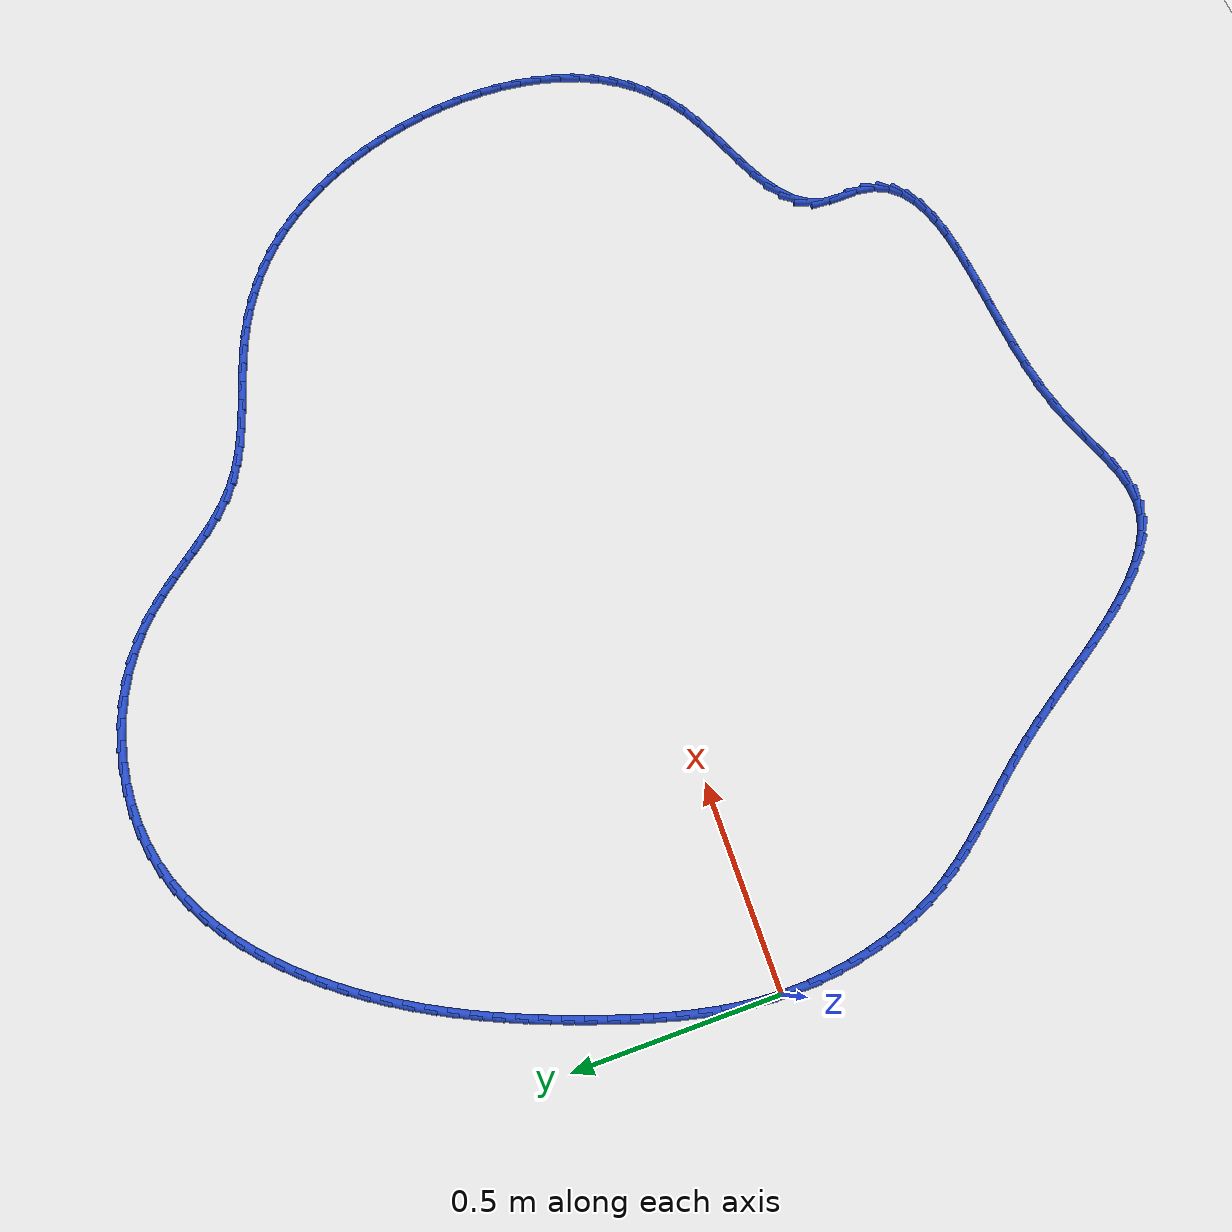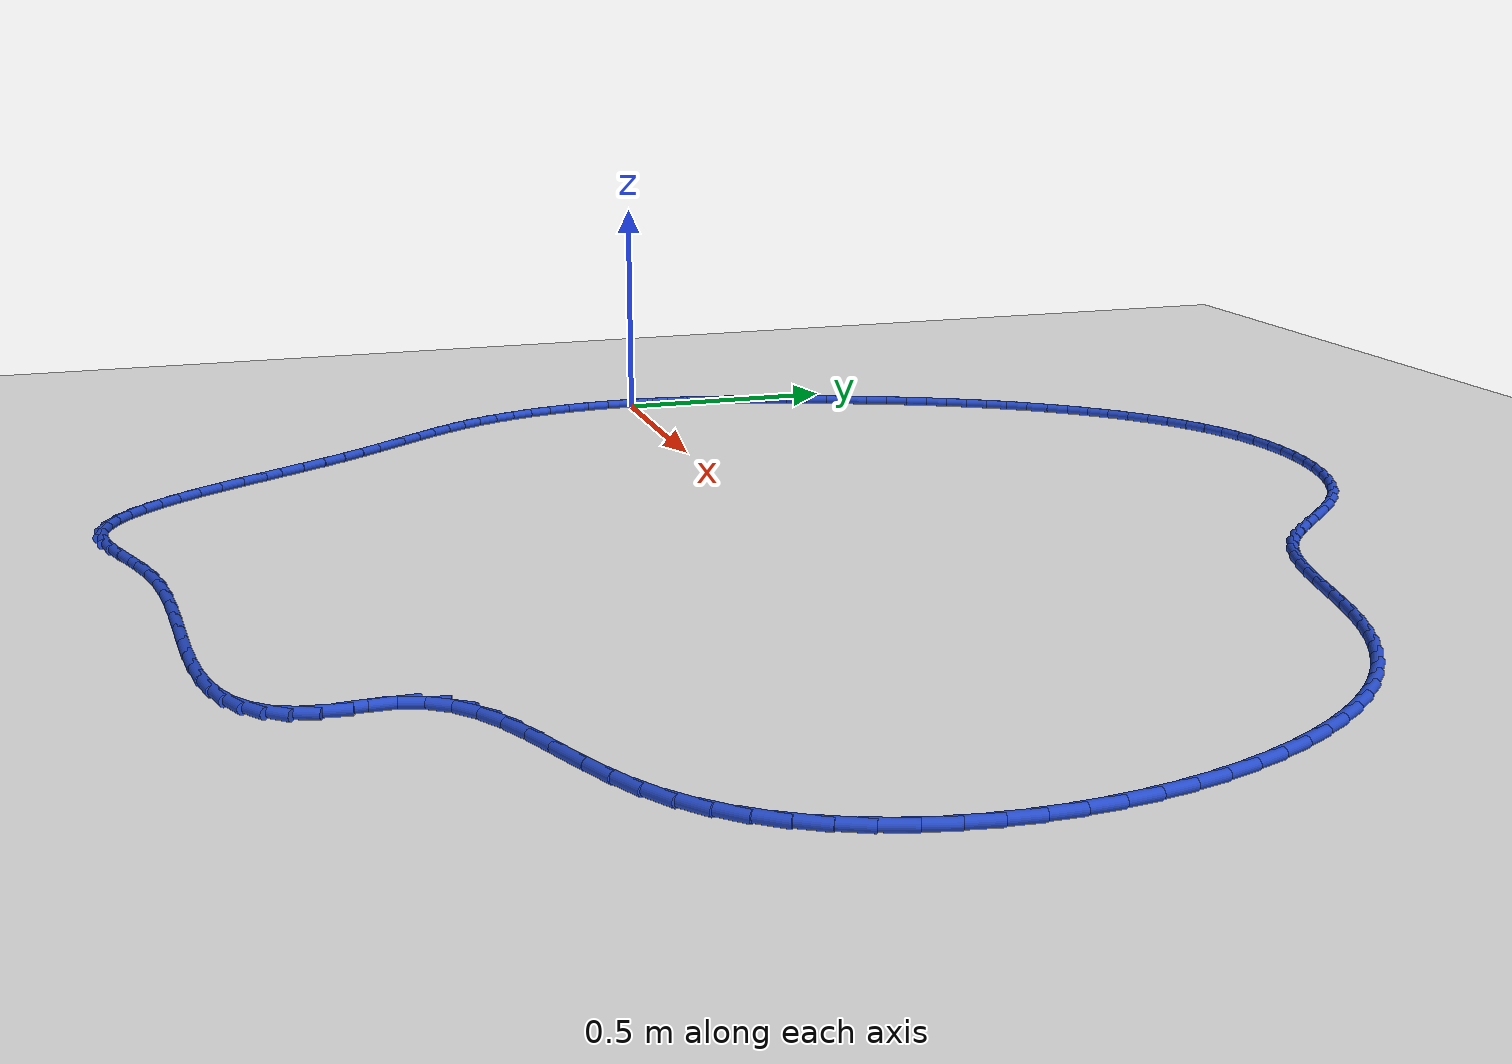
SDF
<sdf version="1.6">
 <world name="default">
  <light name="sun" type="directional">
   <pose>0 0 10 0 -0 0</pose>
   <diffuse>0.8 0.8 0.8 1</diffuse>
   <specular>0.2 0.2 0.2 1</specular>
   <attenuation>
    <range>1000</range>
    <constant>0.9</constant>
    <linear>0.01</linear>
    <quadratic>0.001</quadratic>
   </attenuation>
   <direction>-0.5 0.1 -0.9</direction>
  </light>
  <model name="ground_plane">
   <static>1</static>
   <link name="link">
    <collision name="collision">
     <geometry><plane><normal>0 0 1</normal><size>100 100</size></plane></geometry>
     <surface><friction><ode><mu>100</mu><mu2>50</mu2></ode></friction></surface>
    </collision>
    <visual name="visual">
     <cast_shadows>0</cast_shadows>
     <geometry><plane><normal>0 0 1</normal><size>100 100</size></plane></geometry>
     <material>
      <script><uri>file://media/materials/scripts/gazebo.material</uri><name>Gazebo/WhiteGlow</name></script>
     </material>
    </visual>
   </link>
  </model>
  <gravity>0 0 -9.8</gravity>
  <magnetic_field>6e-06 2.3e-05 -4.2e-05</magnetic_field>
  <atmosphere type="adiabatic"/>
  <physics name="default_physics" default="0" type="ode">
   <max_step_size>0.001</max_step_size>
   <real_time_factor>1</real_time_factor>
   <real_time_update_rate>1000</real_time_update_rate>
  </physics>
  <scene><ambient>0.4 0.4 0.4 1</ambient><background>0.7 0.7 0.7 1</background><shadows>1</shadows></scene>
  <spherical_coordinates>
   <surface_model>EARTH_WGS84</surface_model>
   <latitude_deg>0</latitude_deg>
   <longitude_deg>0</longitude_deg>
   <elevation>0</elevation>
   <heading_deg>0</heading_deg>
  </spherical_coordinates>
  <model name="line">
   <link name="link_0">
    <pose>2.949029909160572e-17 -1.3877787807814457e-17 0.01 0 1.57 1.5125698714163094</pose>
    <collision name="collision">
     <geometry><cylinder><radius>0.01</radius><length>0.08</length></cylinder></geometry>
    </collision>
    <visual name="visual">
     <material>
      <script><name>Gazebo/Blue</name><uri>file://media/materials/scripts/gazebo.material</uri></script>
     </material>
     <geometry><cylinder><radius>0.01</radius><length>0.08</length></cylinder></geometry>
    </visual>
   </link>
   <link name="link_1">
    <pose>0.0029881043514026063 0.05126066307401777 0.01 0 1.57 1.4591487465994732</pose>
    <collision name="collision">
     <geometry><cylinder><radius>0.01</radius><length>0.08</length></cylinder></geometry>
    </collision>
    <visual name="visual">
     <material>
      <script><name>Gazebo/Blue</name><uri>file://media/materials/scripts/gazebo.material</uri></script>
     </material>
     <geometry><cylinder><radius>0.01</radius><length>0.08</length></cylinder></geometry>
    </visual>
   </link>
   <link name="link_2">
    <pose>0.008677130772625843 0.10200397962472153 0.01 0 1.57 1.4109564121631417</pose>
    <collision name="collision">
     <geometry><cylinder><radius>0.01</radius><length>0.08</length></cylinder></geometry>
    </collision>
    <visual name="visual">
     <material>
      <script><name>Gazebo/Blue</name><uri>file://media/materials/scripts/gazebo.material</uri></script>
     </material>
     <geometry><cylinder><radius>0.01</radius><length>0.08</length></cylinder></geometry>
    </visual>
   </link>
   <link name="link_3">
    <pose>0.016781529486799653 0.1522746624679436 0.01 0 1.57 1.3682809262274231</pose>
    <collision name="collision">
     <geometry><cylinder><radius>0.01</radius><length>0.08</length></cylinder></geometry>
    </collision>
    <visual name="visual">
     <material>
      <script><name>Gazebo/Blue</name><uri>file://media/materials/scripts/gazebo.material</uri></script>
     </material>
     <geometry><cylinder><radius>0.01</radius><length>0.08</length></cylinder></geometry>
    </visual>
   </link>
   <link name="link_4">
    <pose>0.027015750717054008 0.20211742441951636 0.01 0 1.57 1.331274907297689</pose>
    <collision name="collision">
     <geometry><cylinder><radius>0.01</radius><length>0.08</length></cylinder></geometry>
    </collision>
    <visual name="visual">
     <material>
      <script><name>Gazebo/Blue</name><uri>file://media/materials/scripts/gazebo.material</uri></script>
     </material>
     <geometry><cylinder><radius>0.01</radius><length>0.08</length></cylinder></geometry>
    </visual>
   </link>
   <link name="link_5">
    <pose>0.03909424468651879 0.2515769782952721 0.01 0 1.57 1.2999916365375197</pose>
    <collision name="collision">
     <geometry><cylinder><radius>0.01</radius><length>0.08</length></cylinder></geometry>
    </collision>
    <visual name="visual">
     <material>
      <script><name>Gazebo/Blue</name><uri>file://media/materials/scripts/gazebo.material</uri></script>
     </material>
     <geometry><cylinder><radius>0.01</radius><length>0.08</length></cylinder></geometry>
    </visual>
   </link>
   <link name="link_6">
    <pose>0.05273146161832403 0.30069803691104313 0.01 0 1.57 1.2744201473961687</pose>
    <collision name="collision">
     <geometry><cylinder><radius>0.01</radius><length>0.08</length></cylinder></geometry>
    </collision>
    <visual name="visual">
     <material>
      <script><name>Gazebo/Blue</name><uri>file://media/materials/scripts/gazebo.material</uri></script>
     </material>
     <geometry><cylinder><radius>0.01</radius><length>0.08</length></cylinder></geometry>
    </visual>
   </link>
   <link name="link_7">
    <pose>0.06764185173559956 0.34952531308266177 0.01 0 1.57 1.2545159372375712</pose>
    <collision name="collision">
     <geometry><cylinder><radius>0.01</radius><length>0.08</length></cylinder></geometry>
    </collision>
    <visual name="visual">
     <material>
      <script><name>Gazebo/Blue</name><uri>file://media/materials/scripts/gazebo.material</uri></script>
     </material>
     <geometry><cylinder><radius>0.01</radius><length>0.08</length></cylinder></geometry>
    </visual>
   </link>
   <link name="link_8">
    <pose>0.08353986526147542 0.39810351962596047 0.01 0 1.57 1.239511197028543</pose>
    <collision name="collision">
     <geometry><cylinder><radius>0.01</radius><length>0.08</length></cylinder></geometry>
    </collision>
    <visual name="visual">
     <material>
      <script><name>Gazebo/Blue</name><uri>file://media/materials/scripts/gazebo.material</uri></script>
     </material>
     <geometry><cylinder><radius>0.01</radius><length>0.08</length></cylinder></geometry>
    </visual>
   </link>
   <link name="link_9">
    <pose>0.10017497771721129 0.44646683063012177 0.01 0 1.57 1.2244391219263737</pose>
    <collision name="collision">
     <geometry><cylinder><radius>0.01</radius><length>0.08</length></cylinder></geometry>
    </collision>
    <visual name="visual">
     <material>
      <script><name>Gazebo/Blue</name><uri>file://media/materials/scripts/gazebo.material</uri></script>
     </material>
     <geometry><cylinder><radius>0.01</radius><length>0.08</length></cylinder></geometry>
    </visual>
   </link>
   <link name="link_10">
    <pose>0.11753813113778437 0.49457676556840946 0.01 0 1.57 1.2071981111151042</pose>
    <collision name="collision">
     <geometry><cylinder><radius>0.01</radius><length>0.08</length></cylinder></geometry>
    </collision>
    <visual name="visual">
     <material>
      <script><name>Gazebo/Blue</name><uri>file://media/materials/scripts/gazebo.material</uri></script>
     </material>
     <geometry><cylinder><radius>0.01</radius><length>0.08</length></cylinder></geometry>
    </visual>
   </link>
   <link name="link_11">
    <pose>0.13572204379259042 0.5423642205655012 0.01 0 1.57 1.1877562584093218</pose>
    <collision name="collision">
     <geometry><cylinder><radius>0.01</radius><length>0.08</length></cylinder></geometry>
    </collision>
    <visual name="visual">
     <material>
      <script><name>Gazebo/Blue</name><uri>file://media/materials/scripts/gazebo.material</uri></script>
     </material>
     <geometry><cylinder><radius>0.01</radius><length>0.08</length></cylinder></geometry>
    </visual>
   </link>
   <link name="link_12">
    <pose>0.15481979094780413 0.5897599843296736 0.01 0 1.57 1.1660896601815167</pose>
    <collision name="collision">
     <geometry><cylinder><radius>0.01</radius><length>0.08</length></cylinder></geometry>
    </collision>
    <visual name="visual">
     <material>
      <script><name>Gazebo/Blue</name><uri>file://media/materials/scripts/gazebo.material</uri></script>
     </material>
     <geometry><cylinder><radius>0.01</radius><length>0.08</length></cylinder></geometry>
    </visual>
   </link>
   <link name="link_13">
    <pose>0.1749244478696 0.6366948455692034 0.01 0 1.57 1.1421779631480247</pose>
    <collision name="collision">
     <geometry><cylinder><radius>0.01</radius><length>0.08</length></cylinder></geometry>
    </collision>
    <visual name="visual">
     <material>
      <script><name>Gazebo/Blue</name><uri>file://media/materials/scripts/gazebo.material</uri></script>
     </material>
     <geometry><cylinder><radius>0.01</radius><length>0.08</length></cylinder></geometry>
    </visual>
   </link>
   <link name="link_14">
    <pose>0.19612908982415264 0.6830995929923676 0.01 0 1.57 1.1160076271777934</pose>
    <collision name="collision">
     <geometry><cylinder><radius>0.01</radius><length>0.08</length></cylinder></geometry>
    </collision>
    <visual name="visual">
     <material>
      <script><name>Gazebo/Blue</name><uri>file://media/materials/scripts/gazebo.material</uri></script>
     </material>
     <geometry><cylinder><radius>0.01</radius><length>0.08</length></cylinder></geometry>
    </visual>
   </link>
   <link name="link_15">
    <pose>0.21852679207763673 0.7289050153074423 0.01 0 1.57 1.0875756077163548</pose>
    <collision name="collision">
     <geometry><cylinder><radius>0.01</radius><length>0.08</length></cylinder></geometry>
    </collision>
    <visual name="visual">
     <material>
      <script><name>Gazebo/Blue</name><uri>file://media/materials/scripts/gazebo.material</uri></script>
     </material>
     <geometry><cylinder><radius>0.01</radius><length>0.08</length></cylinder></geometry>
    </visual>
   </link>
   <link name="link_16">
    <pose>0.24221062989622663 0.7740419012227047 0.01 0 1.57 1.0568934012568016</pose>
    <collision name="collision">
     <geometry><cylinder><radius>0.01</radius><length>0.08</length></cylinder></geometry>
    </collision>
    <visual name="visual">
     <material>
      <script><name>Gazebo/Blue</name><uri>file://media/materials/scripts/gazebo.material</uri></script>
     </material>
     <geometry><cylinder><radius>0.01</radius><length>0.08</length></cylinder></geometry>
    </visual>
   </link>
   <link name="link_17">
    <pose>0.2672736785460973 0.8184410394464315 0.01 0 1.57 1.023991337457359</pose>
    <collision name="collision">
     <geometry><cylinder><radius>0.01</radius><length>0.08</length></cylinder></geometry>
    </collision>
    <visual name="visual">
     <material>
      <script><name>Gazebo/Blue</name><uri>file://media/materials/scripts/gazebo.material</uri></script>
     </material>
     <geometry><cylinder><radius>0.01</radius><length>0.08</length></cylinder></geometry>
    </visual>
   </link>
   <link name="link_18">
    <pose>0.293809013293423 0.8620332186868995 0.01 0 1.57 0.9889229286121084</pose>
    <collision name="collision">
     <geometry><cylinder><radius>0.01</radius><length>0.08</length></cylinder></geometry>
    </collision>
    <visual name="visual">
     <material>
      <script><name>Gazebo/Blue</name><uri>file://media/materials/scripts/gazebo.material</uri></script>
     </material>
     <geometry><cylinder><radius>0.01</radius><length>0.08</length></cylinder></geometry>
    </visual>
   </link>
   <link name="link_19">
    <pose>0.3219097094043786 0.9047492276523851 0.01 0 1.57 0.9517690069361675</pose>
    <collision name="collision">
     <geometry><cylinder><radius>0.01</radius><length>0.08</length></cylinder></geometry>
    </collision>
    <visual name="visual">
     <material>
      <script><name>Gazebo/Blue</name><uri>file://media/materials/scripts/gazebo.material</uri></script>
     </material>
     <geometry><cylinder><radius>0.01</radius><length>0.08</length></cylinder></geometry>
    </visual>
   </link>
   <link name="link_20">
    <pose>0.3516688421451384 0.9465198550511653 0.01 0 1.57 0.9126413031540282</pose>
    <collision name="collision">
     <geometry><cylinder><radius>0.01</radius><length>0.08</length></cylinder></geometry>
    </collision>
    <visual name="visual">
     <material>
      <script><name>Gazebo/Blue</name><uri>file://media/materials/scripts/gazebo.material</uri></script>
     </material>
     <geometry><cylinder><radius>0.01</radius><length>0.08</length></cylinder></geometry>
    </visual>
   </link>
   <link name="link_21">
    <pose>0.3831794867818773 0.9872758895915167 0.01 0 1.57 0.8714439639174862</pose>
    <collision name="collision">
     <geometry><cylinder><radius>0.01</radius><length>0.08</length></cylinder></geometry>
    </collision>
    <visual name="visual">
     <material>
      <script><name>Gazebo/Blue</name><uri>file://media/materials/scripts/gazebo.material</uri></script>
     </material>
     <geometry><cylinder><radius>0.01</radius><length>0.08</length></cylinder></geometry>
    </visual>
   </link>
   <link name="link_22">
    <pose>0.4165256151552607 1.026917885138835 0.01 0 1.57 0.8265497560831557</pose>
    <collision name="collision">
     <geometry><cylinder><radius>0.01</radius><length>0.08</length></cylinder></geometry>
    </collision>
    <visual name="visual">
     <material>
      <script><name>Gazebo/Blue</name><uri>file://media/materials/scripts/gazebo.material</uri></script>
     </material>
     <geometry><cylinder><radius>0.01</radius><length>0.08</length></cylinder></geometry>
    </visual>
   </link>
   <link name="link_23">
    <pose>0.4517312065182593 1.0651471445775287 0.01 0 1.57 0.7768602475495744</pose>
    <collision name="collision">
     <geometry><cylinder><radius>0.01</radius><length>0.08</length></cylinder></geometry>
    </collision>
    <visual name="visual">
     <material>
      <script><name>Gazebo/Blue</name><uri>file://media/materials/scripts/gazebo.material</uri></script>
     </material>
     <geometry><cylinder><radius>0.01</radius><length>0.08</length></cylinder></geometry>
    </visual>
   </link>
   <link name="link_24">
    <pose>0.4887959596824908 1.1015843291336918 0.01 0 1.57 0.7218404898472625</pose>
    <collision name="collision">
     <geometry><cylinder><radius>0.01</radius><length>0.08</length></cylinder></geometry>
    </collision>
    <visual name="visual">
     <material>
      <script><name>Gazebo/Blue</name><uri>file://media/materials/scripts/gazebo.material</uri></script>
     </material>
     <geometry><cylinder><radius>0.01</radius><length>0.08</length></cylinder></geometry>
    </visual>
   </link>
   <link name="link_25">
    <pose>0.5277195049087807 1.135849872358415 0.01 0 1.57 0.660967191001176</pose>
    <collision name="collision">
     <geometry><cylinder><radius>0.01</radius><length>0.08</length></cylinder></geometry>
    </collision>
    <visual name="visual">
     <material>
      <script><name>Gazebo/Blue</name><uri>file://media/materials/scripts/gazebo.material</uri></script>
     </material>
     <geometry><cylinder><radius>0.01</radius><length>0.08</length></cylinder></geometry>
    </visual>
   </link>
   <link name="link_26">
    <pose>0.5685014724579541 1.167564207802787 0.01 0 1.57 0.593774600692492</pose>
    <collision name="collision">
     <geometry><cylinder><radius>0.01</radius><length>0.08</length></cylinder></geometry>
    </collision>
    <visual name="visual">
     <material>
      <script><name>Gazebo/Blue</name><uri>file://media/materials/scripts/gazebo.material</uri></script>
     </material>
     <geometry><cylinder><radius>0.01</radius><length>0.08</length></cylinder></geometry>
    </visual>
   </link>
   <link name="link_27">
    <pose>0.6111414925908366 1.1963477690178983 0.01 0 1.57 0.5199244157419821</pose>
    <collision name="collision">
     <geometry><cylinder><radius>0.01</radius><length>0.08</length></cylinder></geometry>
    </collision>
    <visual name="visual">
     <material>
      <script><name>Gazebo/Blue</name><uri>file://media/materials/scripts/gazebo.material</uri></script>
     </material>
     <geometry><cylinder><radius>0.01</radius><length>0.08</length></cylinder></geometry>
    </visual>
   </link>
   <link name="link_28">
    <pose>0.655639195568253 1.2218209895548389 0.01 0 1.57 0.4392982622570664</pose>
    <collision name="collision">
     <geometry><cylinder><radius>0.01</radius><length>0.08</length></cylinder></geometry>
    </collision>
    <visual name="visual">
     <material>
      <script><name>Gazebo/Blue</name><uri>file://media/materials/scripts/gazebo.material</uri></script>
     </material>
     <geometry><cylinder><radius>0.01</radius><length>0.08</length></cylinder></geometry>
    </visual>
   </link>
   <link name="link_29">
    <pose>0.7019942116510289 1.243604302964698 0.01 0 1.57 0.35210506310100914</pose>
    <collision name="collision">
     <geometry><cylinder><radius>0.01</radius><length>0.08</length></cylinder></geometry>
    </collision>
    <visual name="visual">
     <material>
      <script><name>Gazebo/Blue</name><uri>file://media/materials/scripts/gazebo.material</uri></script>
     </material>
     <geometry><cylinder><radius>0.01</radius><length>0.08</length></cylinder></geometry>
    </visual>
   </link>
   <link name="link_30">
    <pose>0.7502061710999895 1.2613181427985658 0.01 0 1.57 0.25968497393263196</pose>
    <collision name="collision">
     <geometry><cylinder><radius>0.01</radius><length>0.08</length></cylinder></geometry>
    </collision>
    <visual name="visual">
     <material>
      <script><name>Gazebo/Blue</name><uri>file://media/materials/scripts/gazebo.material</uri></script>
     </material>
     <geometry><cylinder><radius>0.01</radius><length>0.08</length></cylinder></geometry>
    </visual>
   </link>
   <link name="link_31">
    <pose>0.8002419381054114 1.2746118580445467 0.01 0 1.57 0.16885310784514004</pose>
    <collision name="collision">
     <geometry><cylinder><radius>0.01</radius><length>0.08</length></cylinder></geometry>
    </collision>
    <visual name="visual">
     <material>
      <script><name>Gazebo/Blue</name><uri>file://media/materials/scripts/gazebo.material</uri></script>
     </material>
     <geometry><cylinder><radius>0.01</radius><length>0.08</length></cylinder></geometry>
    </visual>
   </link>
   <link name="link_32">
    <pose>0.8517718374521479 1.2833964881027002 0.01 0 1.57 0.08215129641691511</pose>
    <collision name="collision">
     <geometry><cylinder><radius>0.01</radius><length>0.08</length></cylinder></geometry>
    </collision>
    <visual name="visual">
     <material>
      <script><name>Gazebo/Blue</name><uri>file://media/materials/scripts/gazebo.material</uri></script>
     </material>
     <geometry><cylinder><radius>0.01</radius><length>0.08</length></cylinder></geometry>
    </visual>
   </link>
   <link name="link_33">
    <pose>0.9043085577632237 1.2877221833019312 0.01 0 1.57 -0.0015418525614981247</pose>
    <collision name="collision">
     <geometry><cylinder><radius>0.01</radius><length>0.08</length></cylinder></geometry>
    </collision>
    <visual name="visual">
     <material>
      <script><name>Gazebo/Blue</name><uri>file://media/materials/scripts/gazebo.material</uri></script>
     </material>
     <geometry><cylinder><radius>0.01</radius><length>0.08</length></cylinder></geometry>
    </visual>
   </link>
   <link name="link_34">
    <pose>0.9573633296927546 1.2876403806011085 0.01 0 1.57 -0.08340674038254943</pose>
    <collision name="collision">
     <geometry><cylinder><radius>0.01</radius><length>0.08</length></cylinder></geometry>
    </collision>
    <visual name="visual">
     <material>
      <script><name>Gazebo/Blue</name><uri>file://media/materials/scripts/gazebo.material</uri></script>
     </material>
     <geometry><cylinder><radius>0.01</radius><length>0.08</length></cylinder></geometry>
    </visual>
   </link>
   <link name="link_35">
    <pose>1.010447383894855 1.2832025169591 0.01 0 1.57 -0.16462588341578888</pose>
    <collision name="collision">
     <geometry><cylinder><radius>0.01</radius><length>0.08</length></cylinder></geometry>
    </collision>
    <visual name="visual">
     <material>
      <script><name>Gazebo/Blue</name><uri>file://media/materials/scripts/gazebo.material</uri></script>
     </material>
     <geometry><cylinder><radius>0.01</radius><length>0.08</length></cylinder></geometry>
    </visual>
   </link>
   <link name="link_36">
    <pose>1.0630719510236415 1.2744600293347752 0.01 0 1.57 -0.2463732302792597</pose>
    <collision name="collision">
     <geometry><cylinder><radius>0.01</radius><length>0.08</length></cylinder></geometry>
    </collision>
    <visual name="visual">
     <material>
      <script><name>Gazebo/Blue</name><uri>file://media/materials/scripts/gazebo.material</uri></script>
     </material>
     <geometry><cylinder><radius>0.01</radius><length>0.08</length></cylinder></geometry>
    </visual>
   </link>
   <link name="link_37">
    <pose>1.1147482617332283 1.2614643546870035 0.01 0 1.57 -0.3298079504636405</pose>
    <collision name="collision">
     <geometry><cylinder><radius>0.01</radius><length>0.08</length></cylinder></geometry>
    </collision>
    <visual name="visual">
     <material>
      <script><name>Gazebo/Blue</name><uri>file://media/materials/scripts/gazebo.material</uri></script>
     </material>
     <geometry><cylinder><radius>0.01</radius><length>0.08</length></cylinder></geometry>
    </visual>
   </link>
   <link name="link_38">
    <pose>1.1649875466777315 1.2442669299746523 0.01 0 1.57 -0.4160630637040997</pose>
    <collision name="collision">
     <geometry><cylinder><radius>0.01</radius><length>0.08</length></cylinder></geometry>
    </collision>
    <visual name="visual">
     <material>
      <script><name>Gazebo/Blue</name><uri>file://media/materials/scripts/gazebo.material</uri></script>
     </material>
     <geometry><cylinder><radius>0.01</radius><length>0.08</length></cylinder></geometry>
    </visual>
   </link>
   <link name="link_39">
    <pose>1.2133010365112664 1.2229191921565914 0.01 0 1.57 -0.5062192141775961</pose>
    <collision name="collision">
     <geometry><cylinder><radius>0.01</radius><length>0.08</length></cylinder></geometry>
    </collision>
    <visual name="visual">
     <material>
      <script><name>Gazebo/Blue</name><uri>file://media/materials/scripts/gazebo.material</uri></script>
     </material>
     <geometry><cylinder><radius>0.01</radius><length>0.08</length></cylinder></geometry>
    </visual>
   </link>
   <link name="link_40">
    <pose>1.2591999618879477 1.1974725781916893 0.01 0 1.57 -0.6012534725056153</pose>
    <collision name="collision">
     <geometry><cylinder><radius>0.01</radius><length>0.08</length></cylinder></geometry>
    </collision>
    <visual name="visual">
     <material>
      <script><name>Gazebo/Blue</name><uri>file://media/materials/scripts/gazebo.material</uri></script>
     </material>
     <geometry><cylinder><radius>0.01</radius><length>0.08</length></cylinder></geometry>
    </visual>
   </link>
   <link name="link_41">
    <pose>1.3021955534618916 1.167978525038814 0.01 0 1.57 -0.7004386972823281</pose>
    <collision name="collision">
     <geometry><cylinder><radius>0.01</radius><length>0.08</length></cylinder></geometry>
    </collision>
    <visual name="visual">
     <material>
      <script><name>Gazebo/Blue</name><uri>file://media/materials/scripts/gazebo.material</uri></script>
     </material>
     <geometry><cylinder><radius>0.01</radius><length>0.08</length></cylinder></geometry>
    </visual>
   </link>
   <link name="link_42">
    <pose>1.3418604926948359 1.1345394506483903 0.01 0 1.57 -0.7839051969775488</pose>
    <collision name="collision">
     <geometry><cylinder><radius>0.01</radius><length>0.08</length></cylinder></geometry>
    </collision>
    <visual name="visual">
     <material>
      <script><name>Gazebo/Blue</name><uri>file://media/materials/scripts/gazebo.material</uri></script>
     </material>
     <geometry><cylinder><radius>0.01</radius><length>0.08</length></cylinder></geometry>
    </visual>
   </link>
   <link name="link_43">
    <pose>1.3785786577234946 1.0979307602339228 0.01 0 1.57 -0.837206322669016</pose>
    <collision name="collision">
     <geometry><cylinder><radius>0.01</radius><length>0.08</length></cylinder></geometry>
    </collision>
    <visual name="visual">
     <material>
      <script><name>Gazebo/Blue</name><uri>file://media/materials/scripts/gazebo.material</uri></script>
     </material>
     <geometry><cylinder><radius>0.01</radius><length>0.08</length></cylinder></geometry>
    </visual>
   </link>
   <link name="link_44">
    <pose>1.413307259133098 1.0594035086845932 0.01 0 1.57 -0.8603867606246717</pose>
    <collision name="collision">
     <geometry><cylinder><radius>0.01</radius><length>0.08</length></cylinder></geometry>
    </collision>
    <visual name="visual">
     <material>
      <script><name>Gazebo/Blue</name><uri>file://media/materials/scripts/gazebo.material</uri></script>
     </material>
     <geometry><cylinder><radius>0.01</radius><length>0.08</length></cylinder></geometry>
    </visual>
   </link>
   <link name="link_45">
    <pose>1.4470155820393797 1.0202187681954809 0.01 0 1.57 -0.8534536272205215</pose>
    <collision name="collision">
     <geometry><cylinder><radius>0.01</radius><length>0.08</length></cylinder></geometry>
    </collision>
    <visual name="visual">
     <material>
      <script><name>Gazebo/Blue</name><uri>file://media/materials/scripts/gazebo.material</uri></script>
     </material>
     <geometry><cylinder><radius>0.01</radius><length>0.08</length></cylinder></geometry>
    </visual>
   </link>
   <link name="link_46">
    <pose>1.4806729115580728 0.9816376109616659 0.01 0 1.57 -0.8154188340893556</pose>
    <collision name="collision">
     <geometry><cylinder><radius>0.01</radius><length>0.08</length></cylinder></geometry>
    </collision>
    <visual name="visual">
     <material>
      <script><name>Gazebo/Blue</name><uri>file://media/materials/scripts/gazebo.material</uri></script>
     </material>
     <geometry><cylinder><radius>0.01</radius><length>0.08</length></cylinder></geometry>
    </visual>
   </link>
   <link name="link_47">
    <pose>1.515248532804911 0.9449211091782278 0.01 0 1.57 -0.7444181057103532</pose>
    <collision name="collision">
     <geometry><cylinder><radius>0.01</radius><length>0.08</length></cylinder></geometry>
    </collision>
    <visual name="visual">
     <material>
      <script><name>Gazebo/Blue</name><uri>file://media/materials/scripts/gazebo.material</uri></script>
     </material>
     <geometry><cylinder><radius>0.01</radius><length>0.08</length></cylinder></geometry>
    </visual>
   </link>
   <link name="link_48">
    <pose>1.5517117308956265 0.9113303350402453 0.01 0 1.57 -0.6389495916548086</pose>
    <collision name="collision">
     <geometry><cylinder><radius>0.01</radius><length>0.08</length></cylinder></geometry>
    </collision>
    <visual name="visual">
     <material>
      <script><name>Gazebo/Blue</name><uri>file://media/materials/scripts/gazebo.material</uri></script>
     </material>
     <geometry><cylinder><radius>0.01</radius><length>0.08</length></cylinder></geometry>
    </visual>
   </link>
   <link name="link_49">
    <pose>1.5910283552620792 0.8821215272711782 0.01 0 1.57 -0.5170822054858782</pose>
    <collision name="collision">
     <geometry><cylinder><radius>0.01</radius><length>0.08</length></cylinder></geometry>
    </collision>
    <visual name="visual">
     <material>
      <script><name>Gazebo/Blue</name><uri>file://media/materials/scripts/gazebo.material</uri></script>
     </material>
     <geometry><cylinder><radius>0.01</radius><length>0.08</length></cylinder></geometry>
    </visual>
   </link>
   <link name="link_50">
    <pose>1.6336780470789674 0.8578669053720684 0.01 0 1.57 -0.41641253473611034</pose>
    <collision name="collision">
     <geometry><cylinder><radius>0.01</radius><length>0.08</length></cylinder></geometry>
    </collision>
    <visual name="visual">
     <material>
      <script><name>Gazebo/Blue</name><uri>file://media/materials/scripts/gazebo.material</uri></script>
     </material>
     <geometry><cylinder><radius>0.01</radius><length>0.08</length></cylinder></geometry>
    </visual>
   </link>
   <link name="link_51">
    <pose>1.6791556487712713 0.8377532305241994 0.01 0 1.57 -0.341616137472867</pose>
    <collision name="collision">
     <geometry><cylinder><radius>0.01</radius><length>0.08</length></cylinder></geometry>
    </collision>
    <visual name="visual">
     <material>
      <script><name>Gazebo/Blue</name><uri>file://media/materials/scripts/gazebo.material</uri></script>
     </material>
     <geometry><cylinder><radius>0.01</radius><length>0.08</length></cylinder></geometry>
    </visual>
   </link>
   <link name="link_52">
    <pose>1.7268369891548891 0.8207998303140017 0.01 0 1.57 -0.29137346187953506</pose>
    <collision name="collision">
     <geometry><cylinder><radius>0.01</radius><length>0.08</length></cylinder></geometry>
    </collision>
    <visual name="visual">
     <material>
      <script><name>Gazebo/Blue</name><uri>file://media/materials/scripts/gazebo.material</uri></script>
     </material>
     <geometry><cylinder><radius>0.01</radius><length>0.08</length></cylinder></geometry>
    </visual>
   </link>
   <link name="link_53">
    <pose>1.7760978970457177 0.8060260323279063 0.01 0 1.57 -0.264017431589229</pose>
    <collision name="collision">
     <geometry><cylinder><radius>0.01</radius><length>0.08</length></cylinder></geometry>
    </collision>
    <visual name="visual">
     <material>
      <script><name>Gazebo/Blue</name><uri>file://media/materials/scripts/gazebo.material</uri></script>
     </material>
     <geometry><cylinder><radius>0.01</radius><length>0.08</length></cylinder></geometry>
    </visual>
   </link>
   <link name="link_54">
    <pose>1.8263142012596543 0.7924511641523437 0.01 0 1.57 -0.2583342014483242</pose>
    <collision name="collision">
     <geometry><cylinder><radius>0.01</radius><length>0.08</length></cylinder></geometry>
    </collision>
    <visual name="visual">
     <material>
      <script><name>Gazebo/Blue</name><uri>file://media/materials/scripts/gazebo.material</uri></script>
     </material>
     <geometry><cylinder><radius>0.01</radius><length>0.08</length></cylinder></geometry>
    </visual>
   </link>
   <link name="link_55">
    <pose>1.8768617306125959 0.7790945533737457 0.01 0 1.57 -0.2738894316777096</pose>
    <collision name="collision">
     <geometry><cylinder><radius>0.01</radius><length>0.08</length></cylinder></geometry>
    </collision>
    <visual name="visual">
     <material>
      <script><name>Gazebo/Blue</name><uri>file://media/materials/scripts/gazebo.material</uri></script>
     </material>
     <geometry><cylinder><radius>0.01</radius><length>0.08</length></cylinder></geometry>
    </visual>
   </link>
   <link name="link_56">
    <pose>1.9271163139204395 0.7649755275785426 0.01 0 1.57 -0.3110469215998444</pose>
    <collision name="collision">
     <geometry><cylinder><radius>0.01</radius><length>0.08</length></cylinder></geometry>
    </collision>
    <visual name="visual">
     <material>
      <script><name>Gazebo/Blue</name><uri>file://media/materials/scripts/gazebo.material</uri></script>
     </material>
     <geometry><cylinder><radius>0.01</radius><length>0.08</length></cylinder></geometry>
    </visual>
   </link>
   <link name="link_57">
    <pose>1.9764543110742427 0.7491142378020027 0.01 0 1.57 -0.36580111199921606</pose>
    <collision name="collision">
     <geometry><cylinder><radius>0.01</radius><length>0.08</length></cylinder></geometry>
    </collision>
    <visual name="visual">
     <material>
      <script><name>Gazebo/Blue</name><uri>file://media/materials/scripts/gazebo.material</uri></script>
     </material>
     <geometry><cylinder><radius>0.01</radius><length>0.08</length></cylinder></geometry>
    </visual>
   </link>
   <link name="link_58">
    <pose>2.024394266530865 0.7307512967466029 0.01 0 1.57 -0.4269735549086533</pose>
    <collision name="collision">
     <geometry><cylinder><radius>0.01</radius><length>0.08</length></cylinder></geometry>
    </collision>
    <visual name="visual">
     <material>
      <script><name>Gazebo/Blue</name><uri>file://media/materials/scripts/gazebo.material</uri></script>
     </material>
     <geometry><cylinder><radius>0.01</radius><length>0.08</length></cylinder></geometry>
    </visual>
   </link>
   <link name="link_59">
    <pose>2.070787895200852 0.7096439084429416 0.01 0 1.57 -0.49266490064206875</pose>
    <collision name="collision">
     <geometry><cylinder><radius>0.01</radius><length>0.08</length></cylinder></geometry>
    </collision>
    <visual name="visual">
     <material>
      <script><name>Gazebo/Blue</name><uri>file://media/materials/scripts/gazebo.material</uri></script>
     </material>
     <geometry><cylinder><radius>0.01</radius><length>0.08</length></cylinder></geometry>
    </visual>
   </link>
   <link name="link_60">
    <pose>2.115534570394699 0.6856231727783874 0.01 0 1.57 -0.5624123535789657</pose>
    <collision name="collision">
     <geometry><cylinder><radius>0.01</radius><length>0.08</length></cylinder></geometry>
    </collision>
    <visual name="visual">
     <material>
      <script><name>Gazebo/Blue</name><uri>file://media/materials/scripts/gazebo.material</uri></script>
     </material>
     <geometry><cylinder><radius>0.01</radius><length>0.08</length></cylinder></geometry>
    </visual>
   </link>
   <link name="link_61">
    <pose>2.1585336654229046 0.6585201896403098 0.01 0 1.57 -0.6355372066139249</pose>
    <collision name="collision">
     <geometry><cylinder><radius>0.01</radius><length>0.08</length></cylinder></geometry>
    </collision>
    <visual name="visual">
     <material>
      <script><name>Gazebo/Blue</name><uri>file://media/materials/scripts/gazebo.material</uri></script>
     </material>
     <geometry><cylinder><radius>0.01</radius><length>0.08</length></cylinder></geometry>
    </visual>
   </link>
   <link name="link_62">
    <pose>2.199684553595964 0.6281660589160778 0.01 0 1.57 -0.7111561845071114</pose>
    <collision name="collision">
     <geometry><cylinder><radius>0.01</radius><length>0.08</length></cylinder></geometry>
    </collision>
    <visual name="visual">
     <material>
      <script><name>Gazebo/Blue</name><uri>file://media/materials/scripts/gazebo.material</uri></script>
     </material>
     <geometry><cylinder><radius>0.01</radius><length>0.08</length></cylinder></geometry>
    </visual>
   </link>
   <link name="link_63">
    <pose>2.2388866082243735 0.5943918804930606 0.01 0 1.57 -0.7882234904319397</pose>
    <collision name="collision">
     <geometry><cylinder><radius>0.01</radius><length>0.08</length></cylinder></geometry>
    </collision>
    <visual name="visual">
     <material>
      <script><name>Gazebo/Blue</name><uri>file://media/materials/scripts/gazebo.material</uri></script>
     </material>
     <geometry><cylinder><radius>0.01</radius><length>0.08</length></cylinder></geometry>
    </visual>
   </link>
   <link name="link_64">
    <pose>2.276039202618631 0.5570287542586275 0.01 0 1.57 -0.8651372965305512</pose>
    <collision name="collision">
     <geometry><cylinder><radius>0.01</radius><length>0.08</length></cylinder></geometry>
    </collision>
    <visual name="visual">
     <material>
      <script><name>Gazebo/Blue</name><uri>file://media/materials/scripts/gazebo.material</uri></script>
     </material>
     <geometry><cylinder><radius>0.01</radius><length>0.08</length></cylinder></geometry>
    </visual>
   </link>
   <link name="link_65">
    <pose>2.311038280999217 0.5159504405210307 0.01 0 1.57 -0.9376949275378799</pose>
    <collision name="collision">
     <geometry><cylinder><radius>0.01</radius><length>0.08</length></cylinder></geometry>
    </collision>
    <visual name="visual">
     <material>
      <script><name>Gazebo/Blue</name><uri>file://media/materials/scripts/gazebo.material</uri></script>
     </material>
     <geometry><cylinder><radius>0.01</radius><length>0.08</length></cylinder></geometry>
    </visual>
   </link>
   <link name="link_66">
    <pose>2.343752235534248 0.4713734675373525 0.01 0 1.57 -1.0050644459832043</pose>
    <collision name="collision">
     <geometry><cylinder><radius>0.01</radius><length>0.08</length></cylinder></geometry>
    </collision>
    <visual name="visual">
     <material>
      <script><name>Gazebo/Blue</name><uri>file://media/materials/scripts/gazebo.material</uri></script>
     </material>
     <geometry><cylinder><radius>0.01</radius><length>0.08</length></cylinder></geometry>
    </visual>
   </link>
   <link name="link_67">
    <pose>2.374036188843586 0.4236794465782663 0.01 0 1.57 -1.0683586394746138</pose>
    <collision name="collision">
     <geometry><cylinder><radius>0.01</radius><length>0.08</length></cylinder></geometry>
    </collision>
    <visual name="visual">
     <material>
      <script><name>Gazebo/Blue</name><uri>file://media/materials/scripts/gazebo.material</uri></script>
     </material>
     <geometry><cylinder><radius>0.01</radius><length>0.08</length></cylinder></geometry>
    </visual>
   </link>
   <link name="link_68">
    <pose>2.4017451784885875 0.37325104710529583 0.01 0 1.57 -1.1286084400754233</pose>
    <collision name="collision">
     <geometry><cylinder><radius>0.01</radius><length>0.08</length></cylinder></geometry>
    </collision>
    <visual name="visual">
     <material>
      <script><name>Gazebo/Blue</name><uri>file://media/materials/scripts/gazebo.material</uri></script>
     </material>
     <geometry><cylinder><radius>0.01</radius><length>0.08</length></cylinder></geometry>
    </visual>
   </link>
   <link name="link_69">
    <pose>2.426734242030611 0.3204709385799638 0.01 0 1.57 -1.1867597768281317</pose>
    <collision name="collision">
     <geometry><cylinder><radius>0.01</radius><length>0.08</length></cylinder></geometry>
    </collision>
    <visual name="visual">
     <material>
      <script><name>Gazebo/Blue</name><uri>file://media/materials/scripts/gazebo.material</uri></script>
     </material>
     <geometry><cylinder><radius>0.01</radius><length>0.08</length></cylinder></geometry>
    </visual>
   </link>
   <link name="link_70">
    <pose>2.4488584170310137 0.2657217904637927 0.01 0 1.57 -1.2436904700492575</pose>
    <collision name="collision">
     <geometry><cylinder><radius>0.01</radius><length>0.08</length></cylinder></geometry>
    </collision>
    <visual name="visual">
     <material>
      <script><name>Gazebo/Blue</name><uri>file://media/materials/scripts/gazebo.material</uri></script>
     </material>
     <geometry><cylinder><radius>0.01</radius><length>0.08</length></cylinder></geometry>
    </visual>
   </link>
   <link name="link_71">
    <pose>2.467972741051153 0.20938627221830505 0.01 0 1.57 -1.3002303840252758</pose>
    <collision name="collision">
     <geometry><cylinder><radius>0.01</radius><length>0.08</length></cylinder></geometry>
    </collision>
    <visual name="visual">
     <material>
      <script><name>Gazebo/Blue</name><uri>file://media/materials/scripts/gazebo.material</uri></script>
     </material>
     <geometry><cylinder><radius>0.01</radius><length>0.08</length></cylinder></geometry>
    </visual>
   </link>
   <link name="link_72">
    <pose>2.483932251652385 0.15184705330502465 0.01 0 1.57 -1.3571819710642343</pose>
    <collision name="collision">
     <geometry><cylinder><radius>0.01</radius><length>0.08</length></cylinder></geometry>
    </collision>
    <visual name="visual">
     <material>
      <script><name>Gazebo/Blue</name><uri>file://media/materials/scripts/gazebo.material</uri></script>
     </material>
     <geometry><cylinder><radius>0.01</radius><length>0.08</length></cylinder></geometry>
    </visual>
   </link>
   <link name="link_73">
    <pose>2.496591986396068 0.09348680318547381 0.01 0 1.57 -1.4153395242383744</pose>
    <collision name="collision">
     <geometry><cylinder><radius>0.01</radius><length>0.08</length></cylinder></geometry>
    </collision>
    <visual name="visual">
     <material>
      <script><name>Gazebo/Blue</name><uri>file://media/materials/scripts/gazebo.material</uri></script>
     </material>
     <geometry><cylinder><radius>0.01</radius><length>0.08</length></cylinder></geometry>
    </visual>
   </link>
   <link name="link_74">
    <pose>2.50580698284356 0.0346881913211753 0.01 0 1.57 -1.4755057776751792</pose>
    <collision name="collision">
     <geometry><cylinder><radius>0.01</radius><length>0.08</length></cylinder></geometry>
    </collision>
    <visual name="visual">
     <material>
      <script><name>Gazebo/Blue</name><uri>file://media/materials/scripts/gazebo.material</uri></script>
     </material>
     <geometry><cylinder><radius>0.01</radius><length>0.08</length></cylinder></geometry>
    </visual>
   </link>
   <link name="link_75">
    <pose>2.5114322785562164 -0.024166112826347744 0.01 0 1.57 -1.5385041409601117</pose>
    <collision name="collision">
     <geometry><cylinder><radius>0.01</radius><length>0.08</length></cylinder></geometry>
    </collision>
    <visual name="visual">
     <material>
      <script><name>Gazebo/Blue</name><uri>file://media/materials/scripts/gazebo.material</uri></script>
     </material>
     <geometry><cylinder><radius>0.01</radius><length>0.08</length></cylinder></geometry>
    </visual>
   </link>
   <link name="link_76">
    <pose>2.5133229110953956 -0.08269343979557332 0.01 0 1.57 1.5364087657211327</pose>
    <collision name="collision">
     <geometry><cylinder><radius>0.01</radius><length>0.08</length></cylinder></geometry>
    </collision>
    <visual name="visual">
     <material>
      <script><name>Gazebo/Blue</name><uri>file://media/materials/scripts/gazebo.material</uri></script>
     </material>
     <geometry><cylinder><radius>0.01</radius><length>0.08</length></cylinder></geometry>
    </visual>
   </link>
   <link name="link_77">
    <pose>2.5113339180224545 -0.14051112012497785 0.01 0 1.57 1.465178604417802</pose>
    <collision name="collision">
     <geometry><cylinder><radius>0.01</radius><length>0.08</length></cylinder></geometry>
    </collision>
    <visual name="visual">
     <material>
      <script><name>Gazebo/Blue</name><uri>file://media/materials/scripts/gazebo.material</uri></script>
     </material>
     <geometry><cylinder><radius>0.01</radius><length>0.08</length></cylinder></geometry>
    </visual>
   </link>
   <link name="link_78">
    <pose>2.505320336898751 -0.1972364843530376 0.01 0 1.57 1.3885329587434143</pose>
    <collision name="collision">
     <geometry><cylinder><radius>0.01</radius><length>0.08</length></cylinder></geometry>
    </collision>
    <visual name="visual">
     <material>
      <script><name>Gazebo/Blue</name><uri>file://media/materials/scripts/gazebo.material</uri></script>
     </material>
     <geometry><cylinder><radius>0.01</radius><length>0.08</length></cylinder></geometry>
    </visual>
   </link>
   <link name="link_79">
    <pose>2.4951372052856415 -0.25248686301823176 0.01 0 1.57 1.3056604258463385</pose>
    <collision name="collision">
     <geometry><cylinder><radius>0.01</radius><length>0.08</length></cylinder></geometry>
    </collision>
    <visual name="visual">
     <material>
      <script><name>Gazebo/Blue</name><uri>file://media/materials/scripts/gazebo.material</uri></script>
     </material>
     <geometry><cylinder><radius>0.01</radius><length>0.08</length></cylinder></geometry>
    </visual>
   </link>
   <link name="link_80">
    <pose>2.480639560744484 -0.3058795866590355 0.01 0 1.57 1.2158880588801633</pose>
    <collision name="collision">
     <geometry><cylinder><radius>0.01</radius><length>0.08</length></cylinder></geometry>
    </collision>
    <visual name="visual">
     <material>
      <script><name>Gazebo/Blue</name><uri>file://media/materials/scripts/gazebo.material</uri></script>
     </material>
     <geometry><cylinder><radius>0.01</radius><length>0.08</length></cylinder></geometry>
    </visual>
   </link>
   <link name="link_81">
    <pose>2.461682440836635 -0.35703198581392764 0.01 0 1.57 1.11880699815043</pose>
    <collision name="collision">
     <geometry><cylinder><radius>0.01</radius><length>0.08</length></cylinder></geometry>
    </collision>
    <visual name="visual">
     <material>
      <script><name>Gazebo/Blue</name><uri>file://media/materials/scripts/gazebo.material</uri></script>
     </material>
     <geometry><cylinder><radius>0.01</radius><length>0.08</length></cylinder></geometry>
    </visual>
   </link>
   <link name="link_82">
    <pose>2.4381208831234527 -0.405561391021385 0.01 0 1.57 1.0144334034402884</pose>
    <collision name="collision">
     <geometry><cylinder><radius>0.01</radius><length>0.08</length></cylinder></geometry>
    </collision>
    <visual name="visual">
     <material>
      <script><name>Gazebo/Blue</name><uri>file://media/materials/scripts/gazebo.material</uri></script>
     </material>
     <geometry><cylinder><radius>0.01</radius><length>0.08</length></cylinder></geometry>
    </visual>
   </link>
   <link name="link_83">
    <pose>2.409809925166294 -0.45108513281988316 0.01 0 1.57 0.9033770725466896</pose>
    <collision name="collision">
     <geometry><cylinder><radius>0.01</radius><length>0.08</length></cylinder></geometry>
    </collision>
    <visual name="visual">
     <material>
      <script><name>Gazebo/Blue</name><uri>file://media/materials/scripts/gazebo.material</uri></script>
     </material>
     <geometry><cylinder><radius>0.01</radius><length>0.08</length></cylinder></geometry>
    </visual>
   </link>
   <link name="link_84">
    <pose>2.376604604526515 -0.4932205417479014 0.01 0 1.57 0.7869614347567963</pose>
    <collision name="collision">
     <geometry><cylinder><radius>0.01</radius><length>0.08</length></cylinder></geometry>
    </collision>
    <visual name="visual">
     <material>
      <script><name>Gazebo/Blue</name><uri>file://media/materials/scripts/gazebo.material</uri></script>
     </material>
     <geometry><cylinder><radius>0.01</radius><length>0.08</length></cylinder></geometry>
    </visual>
   </link>
   <link name="link_85">
    <pose>2.3383599587654755 -0.5315849483439153 0.01 0 1.57 0.6672208792427825</pose>
    <collision name="collision">
     <geometry><cylinder><radius>0.01</radius><length>0.08</length></cylinder></geometry>
    </collision>
    <visual name="visual">
     <material>
      <script><name>Gazebo/Blue</name><uri>file://media/materials/scripts/gazebo.material</uri></script>
     </material>
     <geometry><cylinder><radius>0.01</radius><length>0.08</length></cylinder></geometry>
    </visual>
   </link>
   <link name="link_86">
    <pose>2.2949310254445305 -0.5657956831464033 0.01 0 1.57 0.5488275112734352</pose>
    <collision name="collision">
     <geometry><cylinder><radius>0.01</radius><length>0.08</length></cylinder></geometry>
    </collision>
    <visual name="visual">
     <material>
      <script><name>Gazebo/Blue</name><uri>file://media/materials/scripts/gazebo.material</uri></script>
     </material>
     <geometry><cylinder><radius>0.01</radius><length>0.08</length></cylinder></geometry>
    </visual>
   </link>
   <link name="link_87">
    <pose>2.246273275571209 -0.5955495637181066 0.01 0 1.57 0.4575675801792327</pose>
    <collision name="collision">
     <geometry><cylinder><radius>0.01</radius><length>0.08</length></cylinder></geometry>
    </collision>
    <visual name="visual">
     <material>
      <script><name>Gazebo/Blue</name><uri>file://media/materials/scripts/gazebo.material</uri></script>
     </material>
     <geometry><cylinder><radius>0.01</radius><length>0.08</length></cylinder></geometry>
    </visual>
   </link>
   <link name="link_88">
    <pose>2.1935596489665046 -0.6215069608682916 0.01 0 1.57 0.4046172960775463</pose>
    <collision name="collision">
     <geometry><cylinder><radius>0.01</radius><length>0.08</length></cylinder></geometry>
    </collision>
    <visual name="visual">
     <material>
      <script><name>Gazebo/Blue</name><uri>file://media/materials/scripts/gazebo.material</uri></script>
     </material>
     <geometry><cylinder><radius>0.01</radius><length>0.08</length></cylinder></geometry>
    </visual>
   </link>
   <link name="link_89">
    <pose>2.138772926887928 -0.6449691861323429 0.01 0 1.57 0.3857590403262176</pose>
    <collision name="collision">
     <geometry><cylinder><radius>0.01</radius><length>0.08</length></cylinder></geometry>
    </collision>
    <visual name="visual">
     <material>
      <script><name>Gazebo/Blue</name><uri>file://media/materials/scripts/gazebo.material</uri></script>
     </material>
     <geometry><cylinder><radius>0.01</radius><length>0.08</length></cylinder></geometry>
    </visual>
   </link>
   <link name="link_90">
    <pose>2.0839105266858624 -0.667249134631725 0.01 0 1.57 0.40044242714620226</pose>
    <collision name="collision">
     <geometry><cylinder><radius>0.01</radius><length>0.08</length></cylinder></geometry>
    </collision>
    <visual name="visual">
     <material>
      <script><name>Gazebo/Blue</name><uri>file://media/materials/scripts/gazebo.material</uri></script>
     </material>
     <geometry><cylinder><radius>0.01</radius><length>0.08</length></cylinder></geometry>
    </visual>
   </link>
   <link name="link_91">
    <pose>2.0309698657106896 -0.6896597014879018 0.01 0 1.57 0.45287382496054873</pose>
    <collision name="collision">
     <geometry><cylinder><radius>0.01</radius><length>0.08</length></cylinder></geometry>
    </collision>
    <visual name="visual">
     <material>
      <script><name>Gazebo/Blue</name><uri>file://media/materials/scripts/gazebo.material</uri></script>
     </material>
     <geometry><cylinder><radius>0.01</radius><length>0.08</length></cylinder></geometry>
    </visual>
   </link>
   <link name="link_92">
    <pose>1.981948361312791 -0.7135137818223394 0.01 0 1.57 0.5530735592796258</pose>
    <collision name="collision">
     <geometry><cylinder><radius>0.01</radius><length>0.08</length></cylinder></geometry>
    </collision>
    <visual name="visual">
     <material>
      <script><name>Gazebo/Blue</name><uri>file://media/materials/scripts/gazebo.material</uri></script>
     </material>
     <geometry><cylinder><radius>0.01</radius><length>0.08</length></cylinder></geometry>
    </visual>
   </link>
   <link name="link_93">
    <pose>1.9388434308425495 -0.7401242707565014 0.01 0 1.57 0.7170200916061559</pose>
    <collision name="collision">
     <geometry><cylinder><radius>0.01</radius><length>0.08</length></cylinder></geometry>
    </collision>
    <visual name="visual">
     <material>
      <script><name>Gazebo/Blue</name><uri>file://media/materials/scripts/gazebo.material</uri></script>
     </material>
     <geometry><cylinder><radius>0.01</radius><length>0.08</length></cylinder></geometry>
    </visual>
   </link>
   <link name="link_94">
    <pose>1.9036524916503461 -0.7708040634118536 0.01 0 1.57 0.959398151081952</pose>
    <collision name="collision">
     <geometry><cylinder><radius>0.01</radius><length>0.08</length></cylinder></geometry>
    </collision>
    <visual name="visual">
     <material>
      <script><name>Gazebo/Blue</name><uri>file://media/materials/scripts/gazebo.material</uri></script>
     </material>
     <geometry><cylinder><radius>0.01</radius><length>0.08</length></cylinder></geometry>
    </visual>
   </link>
   <link name="link_95">
    <pose>1.8783729610865643 -0.8068660549098605 0.01 0 1.57 1.2677172473980027</pose>
    <collision name="collision">
     <geometry><cylinder><radius>0.01</radius><length>0.08</length></cylinder></geometry>
    </collision>
    <visual name="visual">
     <material>
      <script><name>Gazebo/Blue</name><uri>file://media/materials/scripts/gazebo.material</uri></script>
     </material>
     <geometry><cylinder><radius>0.01</radius><length>0.08</length></cylinder></geometry>
    </visual>
   </link>
   <link name="link_96">
    <pose>1.8650022565015856 -0.8496231403719858 0.01 0 1.57 1.5566040474890273</pose>
    <collision name="collision">
     <geometry><cylinder><radius>0.01</radius><length>0.08</length></cylinder></geometry>
    </collision>
    <visual name="visual">
     <material>
      <script><name>Gazebo/Blue</name><uri>file://media/materials/scripts/gazebo.material</uri></script>
     </material>
     <geometry><cylinder><radius>0.01</radius><length>0.08</length></cylinder></geometry>
    </visual>
   </link>
   <link name="link_97">
    <pose>1.8642933805228328 -0.8995677876493414 0.01 0 1.57 -1.5256831411513931</pose>
    <collision name="collision">
     <geometry><cylinder><radius>0.01</radius><length>0.08</length></cylinder></geometry>
    </collision>
    <visual name="visual">
     <material>
      <script><name>Gazebo/Blue</name><uri>file://media/materials/scripts/gazebo.material</uri></script>
     </material>
     <geometry><cylinder><radius>0.01</radius><length>0.08</length></cylinder></geometry>
    </visual>
   </link>
   <link name="link_98">
    <pose>1.8665848136001235 -0.9503263037203932 0.01 0 1.57 1.4243070970409963</pose>
    <collision name="collision">
     <geometry><cylinder><radius>0.01</radius><length>0.08</length></cylinder></geometry>
    </collision>
    <visual name="visual">
     <material>
      <script><name>Gazebo/Blue</name><uri>file://media/materials/scripts/gazebo.material</uri></script>
     </material>
     <geometry><cylinder><radius>0.01</radius><length>0.08</length></cylinder></geometry>
    </visual>
   </link>
   <link name="link_99">
    <pose>1.860114745815533 -0.9941774513572158 0.01 0 1.57 1.1431936047824425</pose>
    <collision name="collision">
     <geometry><cylinder><radius>0.01</radius><length>0.08</length></cylinder></geometry>
    </collision>
    <visual name="visual">
     <material>
      <script><name>Gazebo/Blue</name><uri>file://media/materials/scripts/gazebo.material</uri></script>
     </material>
     <geometry><cylinder><radius>0.01</radius><length>0.08</length></cylinder></geometry>
    </visual>
   </link>
   <link name="link_100">
    <pose>1.843593440874991 -1.0304304292501316 0.01 0 1.57 0.8548396531226861</pose>
    <collision name="collision">
     <geometry><cylinder><radius>0.01</radius><length>0.08</length></cylinder></geometry>
    </collision>
    <visual name="visual">
     <material>
      <script><name>Gazebo/Blue</name><uri>file://media/materials/scripts/gazebo.material</uri></script>
     </material>
     <geometry><cylinder><radius>0.01</radius><length>0.08</length></cylinder></geometry>
    </visual>
   </link>
   <link name="link_101">
    <pose>1.8179630386869587 -1.0598927107054599 0.01 0 1.57 0.607160705408578</pose>
    <collision name="collision">
     <geometry><cylinder><radius>0.01</radius><length>0.08</length></cylinder></geometry>
    </collision>
    <visual name="visual">
     <material>
      <script><name>Gazebo/Blue</name><uri>file://media/materials/scripts/gazebo.material</uri></script>
     </material>
     <geometry><cylinder><radius>0.01</radius><length>0.08</length></cylinder></geometry>
    </visual>
   </link>
   <link name="link_102">
    <pose>1.7841656791598959 -1.0833717690295224 0.01 0 1.57 0.41967335676441436</pose>
    <collision name="collision">
     <geometry><cylinder><radius>0.01</radius><length>0.08</length></cylinder></geometry>
    </collision>
    <visual name="visual">
     <material>
      <script><name>Gazebo/Blue</name><uri>file://media/materials/scripts/gazebo.material</uri></script>
     </material>
     <geometry><cylinder><radius>0.01</radius><length>0.08</length></cylinder></geometry>
    </visual>
   </link>
   <link name="link_103">
    <pose>1.7431435022022643 -1.1016750775286386 0.01 0 1.57 0.28647630637574495</pose>
    <collision name="collision">
     <geometry><cylinder><radius>0.01</radius><length>0.08</length></cylinder></geometry>
    </collision>
    <visual name="visual">
     <material>
      <script><name>Gazebo/Blue</name><uri>file://media/materials/scripts/gazebo.material</uri></script>
     </material>
     <geometry><cylinder><radius>0.01</radius><length>0.08</length></cylinder></geometry>
    </visual>
   </link>
   <link name="link_104">
    <pose>1.6958386477225253 -1.1156101095091289 0.01 0 1.57 0.19456572497998023</pose>
    <collision name="collision">
     <geometry><cylinder><radius>0.01</radius><length>0.08</length></cylinder></geometry>
    </collision>
    <visual name="visual">
     <material>
      <script><name>Gazebo/Blue</name><uri>file://media/materials/scripts/gazebo.material</uri></script>
     </material>
     <geometry><cylinder><radius>0.01</radius><length>0.08</length></cylinder></geometry>
    </visual>
   </link>
   <link name="link_105">
    <pose>1.643193255629138 -1.1259843382773138 0.01 0 1.57 0.132810923366068</pose>
    <collision name="collision">
     <geometry><cylinder><radius>0.01</radius><length>0.08</length></cylinder></geometry>
    </collision>
    <visual name="visual">
     <material>
      <script><name>Gazebo/Blue</name><uri>file://media/materials/scripts/gazebo.material</uri></script>
     </material>
     <geometry><cylinder><radius>0.01</radius><length>0.08</length></cylinder></geometry>
    </visual>
   </link>
   <link name="link_106">
    <pose>1.5861494658305648 -1.1336052371395136 0.01 0 1.57 0.09352860309105425</pose>
    <collision name="collision">
     <geometry><cylinder><radius>0.01</radius><length>0.08</length></cylinder></geometry>
    </collision>
    <visual name="visual">
     <material>
      <script><name>Gazebo/Blue</name><uri>file://media/materials/scripts/gazebo.material</uri></script>
     </material>
     <geometry><cylinder><radius>0.01</radius><length>0.08</length></cylinder></geometry>
    </visual>
   </link>
   <link name="link_107">
    <pose>1.5256494182352656 -1.1392802794020491 0.01 0 1.57 0.07187027108714535</pose>
    <collision name="collision">
     <geometry><cylinder><radius>0.01</radius><length>0.08</length></cylinder></geometry>
    </collision>
    <visual name="visual">
     <material>
      <script><name>Gazebo/Blue</name><uri>file://media/materials/scripts/gazebo.material</uri></script>
     </material>
     <geometry><cylinder><radius>0.01</radius><length>0.08</length></cylinder></geometry>
    </visual>
   </link>
   <link name="link_108">
    <pose>1.462635252751701 -1.1438169383712404 0.01 0 1.57 0.06502663162931029</pose>
    <collision name="collision">
     <geometry><cylinder><radius>0.01</radius><length>0.08</length></cylinder></geometry>
    </collision>
    <visual name="visual">
     <material>
      <script><name>Gazebo/Blue</name><uri>file://media/materials/scripts/gazebo.material</uri></script>
     </material>
     <geometry><cylinder><radius>0.01</radius><length>0.08</length></cylinder></geometry>
    </visual>
   </link>
   <link name="link_109">
    <pose>1.3980491092883334 -1.1480226873534072 0.01 0 1.57 0.07167402079669001</pose>
    <collision name="collision">
     <geometry><cylinder><radius>0.01</radius><length>0.08</length></cylinder></geometry>
    </collision>
    <visual name="visual">
     <material>
      <script><name>Gazebo/Blue</name><uri>file://media/materials/scripts/gazebo.material</uri></script>
     </material>
     <geometry><cylinder><radius>0.01</radius><length>0.08</length></cylinder></geometry>
    </visual>
   </link>
   <link name="link_110">
    <pose>1.332833127753622 -1.1527049996548708 0.01 0 1.57 0.09166857086395103</pose>
    <collision name="collision">
     <geometry><cylinder><radius>0.01</radius><length>0.08</length></cylinder></geometry>
    </collision>
    <visual name="visual">
     <material>
      <script><name>Gazebo/Blue</name><uri>file://media/materials/scripts/gazebo.material</uri></script>
     </material>
     <geometry><cylinder><radius>0.01</radius><length>0.08</length></cylinder></geometry>
    </visual>
   </link>
   <link name="link_111">
    <pose>1.267929448056028 -1.158671348581951 0.01 0 1.57 0.1259279853185562</pose>
    <collision name="collision">
     <geometry><cylinder><radius>0.01</radius><length>0.08</length></cylinder></geometry>
    </collision>
    <visual name="visual">
     <material>
      <script><name>Gazebo/Blue</name><uri>file://media/materials/scripts/gazebo.material</uri></script>
     </material>
     <geometry><cylinder><radius>0.01</radius><length>0.08</length></cylinder></geometry>
    </visual>
   </link>
   <link name="link_112">
    <pose>1.2042802101040138 -1.1667292074409685 0.01 0 1.57 0.17644317667961046</pose>
    <collision name="collision">
     <geometry><cylinder><radius>0.01</radius><length>0.08</length></cylinder></geometry>
    </collision>
    <visual name="visual">
     <material>
      <script><name>Gazebo/Blue</name><uri>file://media/materials/scripts/gazebo.material</uri></script>
     </material>
     <geometry><cylinder><radius>0.01</radius><length>0.08</length></cylinder></geometry>
    </visual>
   </link>
   <link name="link_113">
    <pose>1.1428275538060377 -1.1776860495382437 0.01 0 1.57 0.24585545422881322</pose>
    <collision name="collision">
     <geometry><cylinder><radius>0.01</radius><length>0.08</length></cylinder></geometry>
    </collision>
    <visual name="visual">
     <material>
      <script><name>Gazebo/Blue</name><uri>file://media/materials/scripts/gazebo.material</uri></script>
     </material>
     <geometry><cylinder><radius>0.01</radius><length>0.08</length></cylinder></geometry>
    </visual>
   </link>
   <link name="link_114">
    <pose>1.0845022829805844 -1.192321714442202 0.01 0 1.57 0.3151020097592301</pose>
    <collision name="collision">
     <geometry><cylinder><radius>0.01</radius><length>0.08</length></cylinder></geometry>
    </collision>
    <visual name="visual">
     <material>
      <script><name>Gazebo/Blue</name><uri>file://media/materials/scripts/gazebo.material</uri></script>
     </material>
     <geometry><cylinder><radius>0.01</radius><length>0.08</length></cylinder></geometry>
    </visual>
   </link>
   <link name="link_115">
    <pose>1.0297267035908606 -1.2101764876528645 0.01 0 1.57 0.35171115941061765</pose>
    <collision name="collision">
     <geometry><cylinder><radius>0.01</radius><length>0.08</length></cylinder></geometry>
    </collision>
    <visual name="visual">
     <material>
      <script><name>Gazebo/Blue</name><uri>file://media/materials/scripts/gazebo.material</uri></script>
     </material>
     <geometry><cylinder><radius>0.01</radius><length>0.08</length></cylinder></geometry>
    </visual>
   </link>
   <link name="link_116">
    <pose>0.9782204186091009 -1.2290776910022423 0.01 0 1.57 0.3485550529771105</pose>
    <collision name="collision">
     <geometry><cylinder><radius>0.01</radius><length>0.08</length></cylinder></geometry>
    </collision>
    <visual name="visual">
     <material>
      <script><name>Gazebo/Blue</name><uri>file://media/materials/scripts/gazebo.material</uri></script>
     </material>
     <geometry><cylinder><radius>0.01</radius><length>0.08</length></cylinder></geometry>
    </visual>
   </link>
   <link name="link_117">
    <pose>0.9296515753900727 -1.2467272140922776 0.01 0 1.57 0.2976479198444069</pose>
    <collision name="collision">
     <geometry><cylinder><radius>0.01</radius><length>0.08</length></cylinder></geometry>
    </collision>
    <visual name="visual">
     <material>
      <script><name>Gazebo/Blue</name><uri>file://media/materials/scripts/gazebo.material</uri></script>
     </material>
     <geometry><cylinder><radius>0.01</radius><length>0.08</length></cylinder></geometry>
    </visual>
   </link>
   <link name="link_118">
    <pose>0.8836883212885418 -1.2608269465249131 0.01 0 1.57 0.1866753398941896</pose>
    <collision name="collision">
     <geometry><cylinder><radius>0.01</radius><length>0.08</length></cylinder></geometry>
    </collision>
    <visual name="visual">
     <material>
      <script><name>Gazebo/Blue</name><uri>file://media/materials/scripts/gazebo.material</uri></script>
     </material>
     <geometry><cylinder><radius>0.01</radius><length>0.08</length></cylinder></geometry>
    </visual>
   </link>
   <link name="link_119">
    <pose>0.839998803659277 -1.269078777902091 0.01 0 1.57 0.003816149259360909</pose>
    <collision name="collision">
     <geometry><cylinder><radius>0.01</radius><length>0.08</length></cylinder></geometry>
    </collision>
    <visual name="visual">
     <material>
      <script><name>Gazebo/Blue</name><uri>file://media/materials/scripts/gazebo.material</uri></script>
     </material>
     <geometry><cylinder><radius>0.01</radius><length>0.08</length></cylinder></geometry>
    </visual>
   </link>
   <link name="link_120">
    <pose>0.7982540935297469 -1.2692380827200531 0.01 0 1.57 -0.21456412108983422</pose>
    <collision name="collision">
     <geometry><cylinder><radius>0.01</radius><length>0.08</length></cylinder></geometry>
    </collision>
    <visual name="visual">
     <material>
      <script><name>Gazebo/Blue</name><uri>file://media/materials/scripts/gazebo.material</uri></script>
     </material>
     <geometry><cylinder><radius>0.01</radius><length>0.08</length></cylinder></geometry>
    </visual>
   </link>
   <link name="link_121">
    <pose>0.7582045407124556 -1.2605105405771078 0.01 0 1.57 -0.41182244454167877</pose>
    <collision name="collision">
     <geometry><cylinder><radius>0.01</radius><length>0.08</length></cylinder></geometry>
    </collision>
    <visual name="visual">
     <material>
      <script><name>Gazebo/Blue</name><uri>file://media/materials/scripts/gazebo.material</uri></script>
     </material>
     <geometry><cylinder><radius>0.01</radius><length>0.08</length></cylinder></geometry>
    </visual>
   </link>
   <link name="link_122">
    <pose>0.7196870987019232 -1.2436861358995357 0.01 0 1.57 -0.5746195698286974</pose>
    <collision name="collision">
     <geometry><cylinder><radius>0.01</radius><length>0.08</length></cylinder></geometry>
    </collision>
    <visual name="visual">
     <material>
      <script><name>Gazebo/Blue</name><uri>file://media/materials/scripts/gazebo.material</uri></script>
     </material>
     <geometry><cylinder><radius>0.01</radius><length>0.08</length></cylinder></geometry>
    </visual>
   </link>
   <link name="link_123">
    <pose>0.6825431132321799 -1.2196352035802969 0.01 0 1.57 -0.7023462709712291</pose>
    <collision name="collision">
     <geometry><cylinder><radius>0.01</radius><length>0.08</length></cylinder></geometry>
    </collision>
    <visual name="visual">
     <material>
      <script><name>Gazebo/Blue</name><uri>file://media/materials/scripts/gazebo.material</uri></script>
     </material>
     <geometry><cylinder><radius>0.01</radius><length>0.08</length></cylinder></geometry>
    </visual>
   </link>
   <link name="link_124">
    <pose>0.6466139300372584 -1.1892280785123506 0.01 0 1.57 -0.7998101247870321</pose>
    <collision name="collision">
     <geometry><cylinder><radius>0.01</radius><length>0.08</length></cylinder></geometry>
    </collision>
    <visual name="visual">
     <material>
      <script><name>Gazebo/Blue</name><uri>file://media/materials/scripts/gazebo.material</uri></script>
     </material>
     <geometry><cylinder><radius>0.01</radius><length>0.08</length></cylinder></geometry>
    </visual>
   </link>
   <link name="link_125">
    <pose>0.6117408948511913 -1.153335095588657 0.01 0 1.57 -0.872883859291997</pose>
    <collision name="collision">
     <geometry><cylinder><radius>0.01</radius><length>0.08</length></cylinder></geometry>
    </collision>
    <visual name="visual">
     <material>
      <script><name>Gazebo/Blue</name><uri>file://media/materials/scripts/gazebo.material</uri></script>
     </material>
     <geometry><cylinder><radius>0.01</radius><length>0.08</length></cylinder></geometry>
    </visual>
   </link>
   <link name="link_126">
    <pose>0.5777653534080089 -1.1128265897021745 0.01 0 1.57 -0.9266240605434105</pose>
    <collision name="collision">
     <geometry><cylinder><radius>0.01</radius><length>0.08</length></cylinder></geometry>
    </collision>
    <visual name="visual">
     <material>
      <script><name>Gazebo/Blue</name><uri>file://media/materials/scripts/gazebo.material</uri></script>
     </material>
     <geometry><cylinder><radius>0.01</radius><length>0.08</length></cylinder></geometry>
    </visual>
   </link>
   <link name="link_127">
    <pose>0.5445286514417449 -1.0685728957458644 0.01 0 1.57 -0.9648349391312004</pose>
    <collision name="collision">
     <geometry><cylinder><radius>0.01</radius><length>0.08</length></cylinder></geometry>
    </collision>
    <visual name="visual">
     <material>
      <script><name>Gazebo/Blue</name><uri>file://media/materials/scripts/gazebo.material</uri></script>
     </material>
     <geometry><cylinder><radius>0.01</radius><length>0.08</length></cylinder></geometry>
    </visual>
   </link>
   <link name="link_128">
    <pose>0.5118721346864296 -1.0214443486126852 0.01 0 1.57 -0.9901621627644575</pose>
    <collision name="collision">
     <geometry><cylinder><radius>0.01</radius><length>0.08</length></cylinder></geometry>
    </collision>
    <visual name="visual">
     <material>
      <script><name>Gazebo/Blue</name><uri>file://media/materials/scripts/gazebo.material</uri></script>
     </material>
     <geometry><cylinder><radius>0.01</radius><length>0.08</length></cylinder></geometry>
    </visual>
   </link>
   <link name="link_129">
    <pose>0.47963714887609576 -0.9723112831955967 0.01 0 1.57 -1.0042956801958862</pose>
    <collision name="collision">
     <geometry><cylinder><radius>0.01</radius><length>0.08</length></cylinder></geometry>
    </collision>
    <visual name="visual">
     <material>
      <script><name>Gazebo/Blue</name><uri>file://media/materials/scripts/gazebo.material</uri></script>
     </material>
     <geometry><cylinder><radius>0.01</radius><length>0.08</length></cylinder></geometry>
    </visual>
   </link>
   <link name="link_130">
    <pose>0.4476650397447755 -0.9220440343875593 0.01 0 1.57 -1.0081380290167339</pose>
    <collision name="collision">
     <geometry><cylinder><radius>0.01</radius><length>0.08</length></cylinder></geometry>
    </collision>
    <visual name="visual">
     <material>
      <script><name>Gazebo/Blue</name><uri>file://media/materials/scripts/gazebo.material</uri></script>
     </material>
     <geometry><cylinder><radius>0.01</radius><length>0.08</length></cylinder></geometry>
    </visual>
   </link>
   <link name="link_131">
    <pose>0.41579715302650005 -0.8715129370815315 0.01 0 1.57 -1.0019014777335034</pose>
    <collision name="collision">
     <geometry><cylinder><radius>0.01</radius><length>0.08</length></cylinder></geometry>
    </collision>
    <visual name="visual">
     <material>
      <script><name>Gazebo/Blue</name><uri>file://media/materials/scripts/gazebo.material</uri></script>
     </material>
     <geometry><cylinder><radius>0.01</radius><length>0.08</length></cylinder></geometry>
    </visual>
   </link>
   <link name="link_132">
    <pose>0.38387483445530207 -0.8215883261704742 0.01 0 1.57 -0.9851283186025045</pose>
    <collision name="collision">
     <geometry><cylinder><radius>0.01</radius><length>0.08</length></cylinder></geometry>
    </collision>
    <visual name="visual">
     <material>
      <script><name>Gazebo/Blue</name><uri>file://media/materials/scripts/gazebo.material</uri></script>
     </material>
     <geometry><cylinder><radius>0.01</radius><length>0.08</length></cylinder></geometry>
    </visual>
   </link>
   <link name="link_133">
    <pose>0.35173942976521255 -0.7731405365473455 0.01 0 1.57 -0.9568128150489336</pose>
    <collision name="collision">
     <geometry><cylinder><radius>0.01</radius><length>0.08</length></cylinder></geometry>
    </collision>
    <visual name="visual">
     <material>
      <script><name>Gazebo/Blue</name><uri>file://media/materials/scripts/gazebo.material</uri></script>
     </material>
     <geometry><cylinder><radius>0.01</radius><length>0.08</length></cylinder></geometry>
    </visual>
   </link>
   <link name="link_134">
    <pose>0.31923660659133146 -0.7270284018645867 0.01 0 1.57 -0.9247369917217855</pose>
    <collision name="collision">
     <geometry><cylinder><radius>0.01</radius><length>0.08</length></cylinder></geometry>
    </collision>
    <visual name="visual">
     <material>
      <script><name>Gazebo/Blue</name><uri>file://media/materials/scripts/gazebo.material</uri></script>
     </material>
     <geometry><cylinder><radius>0.01</radius><length>0.08</length></cylinder></geometry>
    </visual>
   </link>
   <link name="link_135">
    <pose>0.286433037947484 -0.6835226266210365 0.01 0 1.57 -0.9030521549331368</pose>
    <collision name="collision">
     <geometry><cylinder><radius>0.01</radius><length>0.08</length></cylinder></geometry>
    </collision>
    <visual name="visual">
     <material>
      <script><name>Gazebo/Blue</name><uri>file://media/materials/scripts/gazebo.material</uri></script>
     </material>
     <geometry><cylinder><radius>0.01</radius><length>0.08</length></cylinder></geometry>
    </visual>
   </link>
   <link name="link_136">
    <pose>0.25371757497693054 -0.6420365499804969 0.01 0 1.57 -0.894288738235678</pose>
    <collision name="collision">
     <geometry><cylinder><radius>0.01</radius><length>0.08</length></cylinder></geometry>
    </collision>
    <visual name="visual">
     <material>
      <script><name>Gazebo/Blue</name><uri>file://media/materials/scripts/gazebo.material</uri></script>
     </material>
     <geometry><cylinder><radius>0.01</radius><length>0.08</length></cylinder></geometry>
    </visual>
   </link>
   <link name="link_137">
    <pose>0.22150453076063517 -0.6019157529917623 0.01 0 1.57 -0.8996495891364626</pose>
    <collision name="collision">
     <geometry><cylinder><radius>0.01</radius><length>0.08</length></cylinder></geometry>
    </collision>
    <visual name="visual">
     <material>
      <script><name>Gazebo/Blue</name><uri>file://media/materials/scripts/gazebo.material</uri></script>
     </material>
     <geometry><cylinder><radius>0.01</radius><length>0.08</length></cylinder></geometry>
    </visual>
   </link>
   <link name="link_138">
    <pose>0.19020821837956206 -0.5625058167036272 0.01 0 1.57 -0.920014655037656</pose>
    <collision name="collision">
     <geometry><cylinder><radius>0.01</radius><length>0.08</length></cylinder></geometry>
    </collision>
    <visual name="visual">
     <material>
      <script><name>Gazebo/Blue</name><uri>file://media/materials/scripts/gazebo.material</uri></script>
     </material>
     <geometry><cylinder><radius>0.01</radius><length>0.08</length></cylinder></geometry>
    </visual>
   </link>
   <link name="link_139">
    <pose>0.16024295091467333 -0.5231523221648832 0.01 0 1.57 -0.9558181895094806</pose>
    <collision name="collision">
     <geometry><cylinder><radius>0.01</radius><length>0.08</length></cylinder></geometry>
    </collision>
    <visual name="visual">
     <material>
      <script><name>Gazebo/Blue</name><uri>file://media/materials/scripts/gazebo.material</uri></script>
     </material>
     <geometry><cylinder><radius>0.01</radius><length>0.08</length></cylinder></geometry>
    </visual>
   </link>
   <link name="link_140">
    <pose>0.13202304144693347 -0.4832008504243251 0.01 0 1.57 -1.006842864763621</pose>
    <collision name="collision">
     <geometry><cylinder><radius>0.01</radius><length>0.08</length></cylinder></geometry>
    </collision>
    <visual name="visual">
     <material>
      <script><name>Gazebo/Blue</name><uri>file://media/materials/scripts/gazebo.material</uri></script>
     </material>
     <geometry><cylinder><radius>0.01</radius><length>0.08</length></cylinder></geometry>
    </visual>
   </link>
   <link name="link_141">
    <pose>0.10596280305730507 -0.44199698253074543 0.01 0 1.57 -1.0719459476015227</pose>
    <collision name="collision">
     <geometry><cylinder><radius>0.01</radius><length>0.08</length></cylinder></geometry>
    </collision>
    <visual name="visual">
     <material>
      <script><name>Gazebo/Blue</name><uri>file://media/materials/scripts/gazebo.material</uri></script>
     </material>
     <geometry><cylinder><radius>0.01</radius><length>0.08</length></cylinder></geometry>
    </visual>
   </link>
   <link name="link_142">
    <pose>0.08247616648138809 -0.39888726321542006 0.01 0 1.57 -1.1446374311916854</pose>
    <collision name="collision">
     <geometry><cylinder><radius>0.01</radius><length>0.08</length></cylinder></geometry>
    </collision>
    <visual name="visual">
     <material>
      <script><name>Gazebo/Blue</name><uri>file://media/materials/scripts/gazebo.material</uri></script>
     </material>
     <geometry><cylinder><radius>0.01</radius><length>0.08</length></cylinder></geometry>
    </visual>
   </link>
   <link name="link_143">
    <pose>0.06186805959061983 -0.35349297350990333 0.01 0 1.57 -1.213763336383752</pose>
    <collision name="collision">
     <geometry><cylinder><radius>0.01</radius><length>0.08</length></cylinder></geometry>
    </collision>
    <visual name="visual">
     <material>
      <script><name>Gazebo/Blue</name><uri>file://media/materials/scripts/gazebo.material</uri></script>
     </material>
     <geometry><cylinder><radius>0.01</radius><length>0.08</length></cylinder></geometry>
    </visual>
   </link>
   <link name="link_144">
    <pose>0.04418479839341294 -0.30608721279016304 0.01 0 1.57 -1.2786899438000445</pose>
    <collision name="collision">
     <geometry><cylinder><radius>0.01</radius><length>0.08</length></cylinder></geometry>
    </collision>
    <visual name="visual">
     <material>
      <script><name>Gazebo/Blue</name><uri>file://media/materials/scripts/gazebo.material</uri></script>
     </material>
     <geometry><cylinder><radius>0.01</radius><length>0.08</length></cylinder></geometry>
    </visual>
   </link>
   <link name="link_145">
    <pose>0.02943518662592928 -0.2570376282495394 0.01 0 1.57 -1.3403496227027523</pose>
    <collision name="collision">
     <geometry><cylinder><radius>0.01</radius><length>0.08</length></cylinder></geometry>
    </collision>
    <visual name="visual">
     <material>
      <script><name>Gazebo/Blue</name><uri>file://media/materials/scripts/gazebo.material</uri></script>
     </material>
     <geometry><cylinder><radius>0.01</radius><length>0.08</length></cylinder></geometry>
    </visual>
   </link>
   <link name="link_146">
    <pose>0.017628028024329667 -0.20671186708136915 0.01 0 1.57 -1.3996364977760698</pose>
    <collision name="collision">
     <geometry><cylinder><radius>0.01</radius><length>0.08</length></cylinder></geometry>
    </collision>
    <visual name="visual">
     <material>
      <script><name>Gazebo/Blue</name><uri>file://media/materials/scripts/gazebo.material</uri></script>
     </material>
     <geometry><cylinder><radius>0.01</radius><length>0.08</length></cylinder></geometry>
    </visual>
   </link>
   <link name="link_147">
    <pose>0.008772126324775663 -0.1554775764789915 0.01 0 1.57 -1.457410839412179</pose>
    <collision name="collision">
     <geometry><cylinder><radius>0.01</radius><length>0.08</length></cylinder></geometry>
    </collision>
    <visual name="visual">
     <material>
      <script><name>Gazebo/Blue</name><uri>file://media/materials/scripts/gazebo.material</uri></script>
     </material>
     <geometry><cylinder><radius>0.01</radius><length>0.08</length></cylinder></geometry>
    </visual>
   </link>
   <link name="link_148">
    <pose>0.002876285263428607 -0.10370240363574566 0.01 0 1.57 -1.514511922141512</pose>
    <collision name="collision">
     <geometry><cylinder><radius>0.01</radius><length>0.08</length></cylinder></geometry>
    </collision>
    <visual name="visual">
     <material>
      <script><name>Gazebo/Blue</name><uri>file://media/materials/scripts/gazebo.material</uri></script>
     </material>
     <geometry><cylinder><radius>0.01</radius><length>0.08</length></cylinder></geometry>
    </visual>
   </link>
   <link name="link_149">
    <pose>-5.069142355039469e-05 -0.05175399574496848 0.01 0 1.57 1.5698168583188814</pose>
    <collision name="collision">
     <geometry><cylinder><radius>0.01</radius><length>0.08</length></cylinder></geometry>
    </collision>
    <visual name="visual">
     <material>
      <script><name>Gazebo/Blue</name><uri>file://media/materials/scripts/gazebo.material</uri></script>
     </material>
     <geometry><cylinder><radius>0.01</radius><length>0.08</length></cylinder></geometry>
    </visual>
   </link>
   <link name="link_150">
    <pose>4.683753385137379e-17 -6.938893903907228e-17 0.01 0 1.57 1.511536852287462</pose>
    <collision name="collision">
     <geometry><cylinder><radius>0.01</radius><length>0.08</length></cylinder></geometry>
    </collision>
    <visual name="visual">
     <material>
      <script><name>Gazebo/Blue</name><uri>file://media/materials/scripts/gazebo.material</uri></script>
     </material>
     <geometry><cylinder><radius>0.01</radius><length>0.08</length></cylinder></geometry>
    </visual>
   </link>
   <link name="link_151">
    <pose>0.003037163270241297 0.05119193640582377 0.01 0 1.57 1.5115368522874615</pose>
    <collision name="collision">
     <geometry><cylinder><radius>0.01</radius><length>0.08</length></cylinder></geometry>
    </collision>
    <visual name="visual">
     <material>
      <script><name>Gazebo/Blue</name><uri>file://media/materials/scripts/gazebo.material</uri></script>
     </material>
     <geometry><cylinder><radius>0.01</radius><length>0.08</length></cylinder></geometry>
    </visual>
   </link>
  </model>
 </world>
</sdf>
